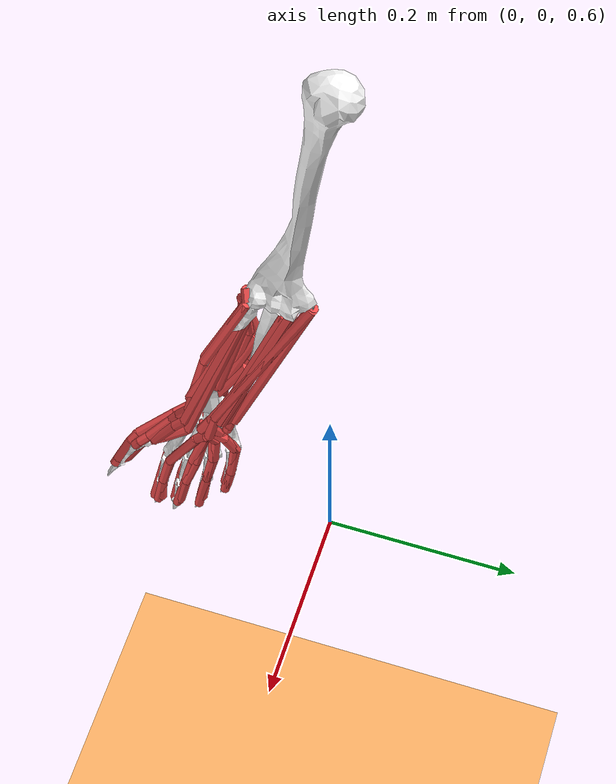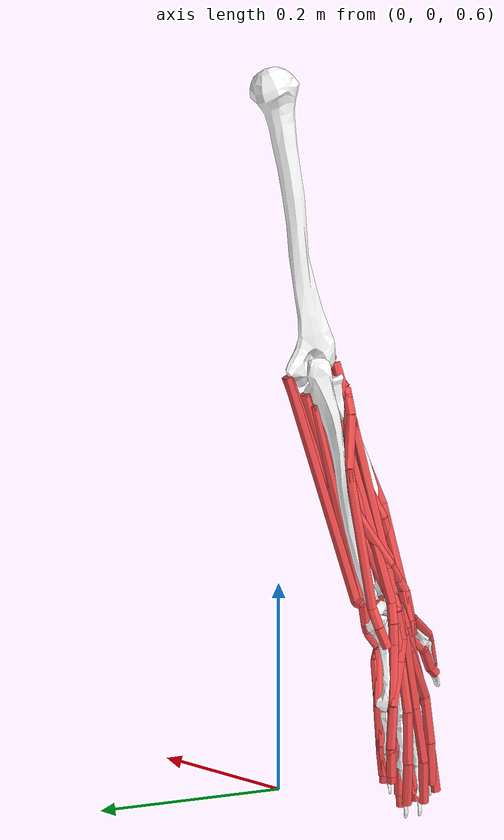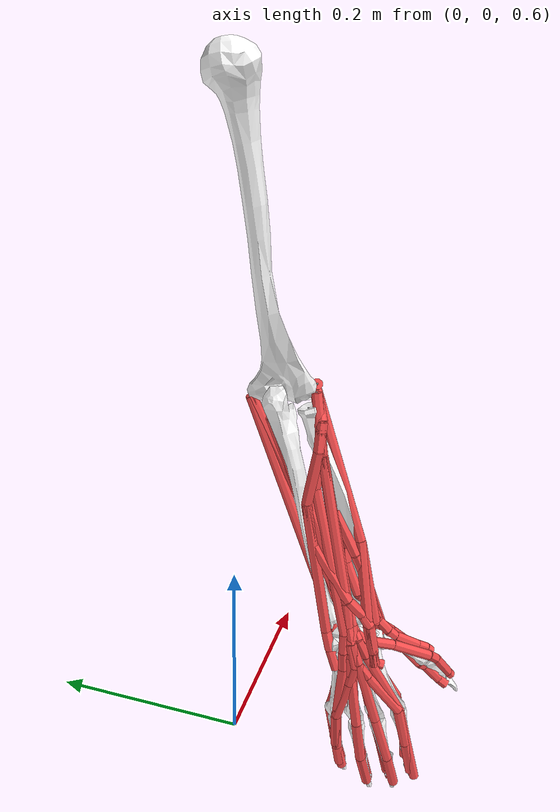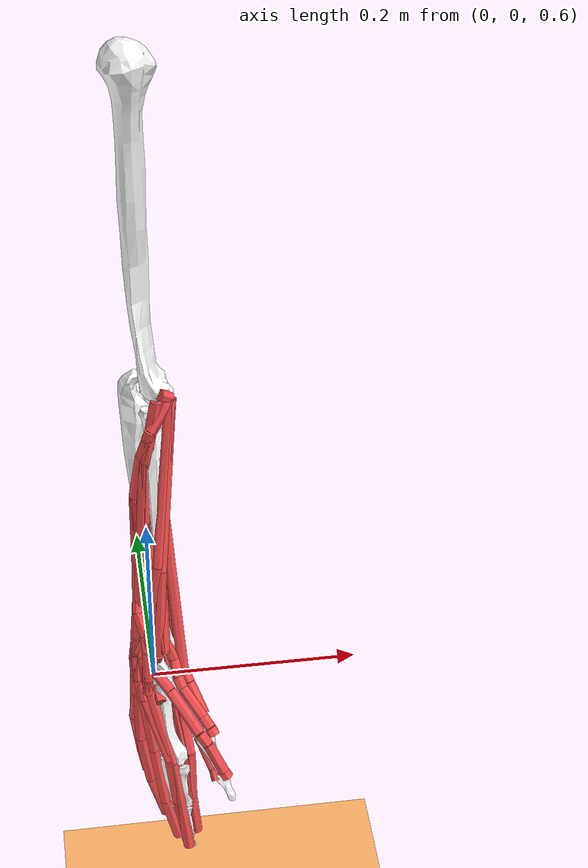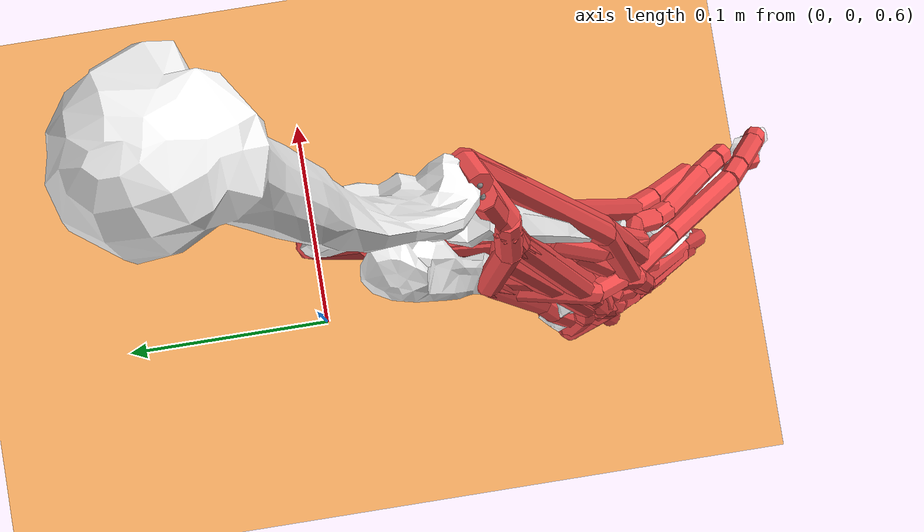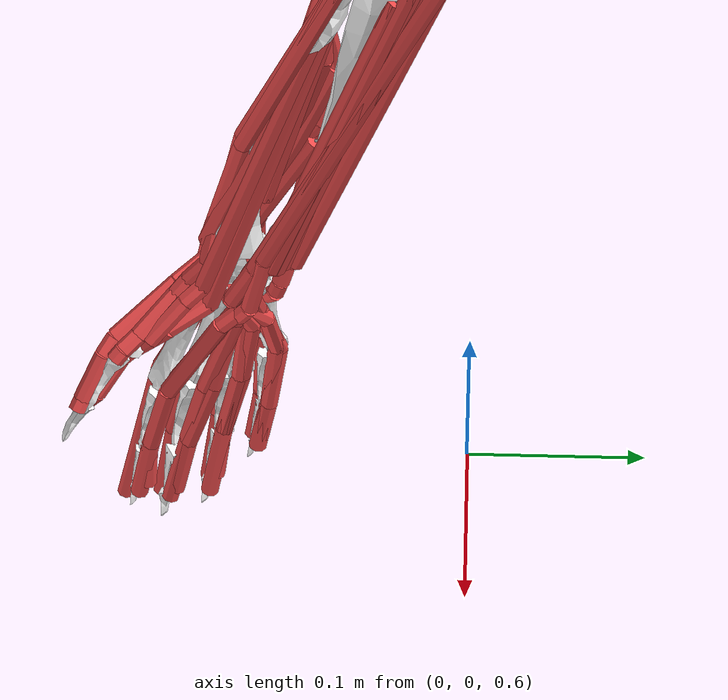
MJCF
<mujoco model="template">
  <!-- This model has been converted from an OpenSim model. Model conversion by MyoConverter https://github.com/MyoHub/myoconverter. This model is licensed under Apache 2.0. -->
  <compiler angle="radian" autolimits="true"/>
  <option timestep="0.005"/>
  <size njmax="1000" nconmax="400" nkey="1" nuser_jnt="1"/>
  <visual>
    <scale framelength="0.5" framewidth="0.01"/>
  </visual>
  <statistic meansize="0.0480678" extent="2.30764" center="0 0 0.153819"/>
  <default class="main">
    <joint limited="true" armature="1e-05" damping="0.05"/>
    <geom margin="0.001" rgba="0.8 0.6 0.4 1"/>
    <site size="0.001 0.005 0.005"/>
    <tendon limited="false" width="0.005" rgba="0.95 0.3 0.3 1"/>
    <default class="muscle">
      <general ctrllimited="true" ctrlrange="0 1" dyntype="muscle" gaintype="muscle" biastype="muscle" dynprm="0.01 0.04 0 0 0 0 0 0 0 0" gainprm="0.75 1.05 -1 200 0.5 1.6 1.5 1.3 1.2 0" biasprm="0.75 1.05 -1 200 0.5 1.6 1.5 1.3 1.2 0"/>
    </default>
    <default class="motor">
      <general gainprm="5 0 0 0 0 0 0 0 0 0"/>
    </default>
  </default>
  <asset>
    <texture type="skybox" builtin="gradient" rgb1="1 1 1" rgb2="0.6 0.8 1" width="256" height="1536"/>
    <mesh name="ground_geom_1_humerus" file="Geometry\humerus.stl"/>
    <mesh name="ulna_geom_1_ulna" file="Geometry\ulna.stl"/>
    <mesh name="radius_geom_1_radius" file="Geometry\radius.stl"/>
    <mesh name="trapezium_geom_1_r_trpzm" file="Geometry\r_trpzm.stl"/>
    <mesh name="trapezoid_geom_1_r_trpzd" file="Geometry\r_trpzd.stl"/>
    <mesh name="capitate_geom_1_r_cap" file="Geometry\r_cap.stl"/>
    <mesh name="hamate_geom_1_r_ham" file="Geometry\r_ham.stl"/>
    <mesh name="metacarpal2_geom_1_fingers1" file="Geometry\fingers1.stl"/>
    <mesh name="Iphalanx1_geom_1_fingers2" file="Geometry\fingers2.stl"/>
    <mesh name="Iphalanx2_geom_1_fingers3" file="Geometry\fingers3.stl"/>
    <mesh name="Iphalanx3_geom_1_fingers4" file="Geometry\fingers4.stl"/>
    <mesh name="metacarpal3_geom_1_fingers8" file="Geometry\fingers8.stl"/>
    <mesh name="midfinger_geom_1_fingers6" file="Geometry\fingers6.stl"/>
    <mesh name="midfinger_geom_2_fingers7" file="Geometry\fingers7.stl"/>
    <mesh name="midfinger_geom_3_fingers5" file="Geometry\fingers5.stl"/>
    <mesh name="metacarpal4_geom_1_fingers12" file="Geometry\fingers12.stl"/>
    <mesh name="ringfinger_geom_1_fingers10" file="Geometry\fingers10.stl"/>
    <mesh name="ringfinger_geom_2_fingers11" file="Geometry\fingers11.stl"/>
    <mesh name="ringfinger_geom_3_fingers9" file="Geometry\fingers9.stl"/>
    <mesh name="metacarpal5_geom_1_fingers16" file="Geometry\fingers16.stl"/>
    <mesh name="littlefinger_geom_1_fingers14" file="Geometry\fingers14.stl"/>
    <mesh name="littlefinger_geom_2_fingers15" file="Geometry\fingers15.stl"/>
    <mesh name="littlefinger_geom_3_fingers13" file="Geometry\fingers13.stl"/>
    <mesh name="thumb_geom_1_fingers17" file="Geometry\fingers17.stl"/>
    <mesh name="thumb_geom_2_fingers18" file="Geometry\fingers18.stl"/>
    <mesh name="thumb_geom_3_fingers19" file="Geometry\fingers19.stl"/>
    <mesh name="scaphoid_geom_1_r_scaph" file="Geometry\r_scaph.stl"/>
    <mesh name="lunate_geom_1_r_lun" file="Geometry\r_lun.stl"/>
    <mesh name="pisiform_geom_1_r_pis" file="Geometry\r_pis.stl"/>
    <mesh name="triquetrum_geom_1_r_triq" file="Geometry\r_triq.stl"/>
  </asset>
  <worldbody>
    <light pos="0 0 0" dir="0 0 -1" directional="true"/>
    <body name="ground" quat="0.707035 0.707179 0 0">
      <geom name="ground-plane" size="10 10 0.125" quat="0.707035 -0.707179 0 0" type="plane" rgba="1 0.7 0.4 1"/>
      <geom name="ground_geom_1" pos="0 1.274 0" type="mesh" rgba="1 1 1 1" mesh="ground_geom_1_humerus"/>
      <site name="FCR_FCR-P1" pos="0.00639 0.99639 0.01313"/>
      <site name="FCU_FCU-P1" pos="0.00463 0.99632 0.01318"/>
      <site name="ECU_pre-surgery_ECU_pre-surgery-P1" pos="0.02268 1.00596 0.06679"/>
      <site name="ECU_post-surgery_ECU_post-surgery-P1" pos="0.02268 1.00596 0.06679"/>
      <site name="EDM_EDM-P1" pos="0.02257 1.00608 0.06683"/>
      <site name="ECRB_ECRB-P1" pos="0.02254 1.00587 0.06679"/>
      <site name="ECRL_ECRL-P1" pos="0.01337 1.01289 0.07069"/>
      <site name="ECRL_ECRL-P2" pos="0.02239 1.00566 0.06679"/>
      <site name="FDSI_FDSI-P1" pos="0.0035 0.97945 0.03226"/>
      <site name="FDSM_FDSM-P1" pos="0.0035 0.97945 0.03226"/>
      <site name="FDSR_FDSR-P1" pos="0.0035 0.97945 0.03226"/>
      <site name="FDSL_FDSL-P1" pos="0.0035 0.97945 0.03226"/>
      <site name="EDCL_EDCL-P1" pos="0.01056 1.00611 0.07127"/>
      <site name="EDCR_EDCR-P1" pos="0.01011 1.00611 0.07127"/>
      <site name="EDCM_EDCM-P1" pos="0.01011 1.00611 0.07127"/>
      <site name="EDCI_EDCI-P1" pos="0.01011 1.00611 0.07127"/>
      <site name="PL_PL-P1" pos="0.00468 0.99702 0.01316"/>
    </body>
    <body name="ulna" pos="0.0127 -0.0389 1" quat="0.707035 0.707179 0 0">
      <inertial pos="0 0 0" mass="0.001" diaginertia="0.001 0.001 0.001"/>
      <joint name="elbow_flexion" pos="0 0 0" axis="0.226004 0.191003 0.955217" limited="false" range="0 2.269" damping="0"/>
      <geom name="ulna_geom_1" type="mesh" rgba="1 1 1 1" mesh="ulna_geom_1_ulna"/>
      <site name="FCU_FCU-P2" pos="-0.00465 -0.22771 0.05589"/>
      <site name="FCU_FCU-P3" pos="-0.01368 -0.22899 0.05805"/>
      <site name="ECU_pre-surgery_ECU_pre-surgery-P4" pos="-0.02457 -0.09422 0.03348"/>
      <site name="ECU_pre-surgery_ECU_pre-surgery-P5" pos="-0.02793 -0.23106 0.05873"/>
      <site name="ECU_post-surgery_ECU_post-surgery-P4" pos="-0.02457 -0.09422 0.03348"/>
      <site name="ECU_post-surgery_ECU_post-surgery-P5" pos="-0.02463 -0.1364 0.04159"/>
      <site name="ECU_post-surgery_ECU_post-surgery-P6" pos="-0.02953 -0.18933 0.07846"/>
      <site name="EDM_EDM-P4" pos="-0.03277 -0.22628 0.07769"/>
      <site name="FDPI_FDPI-P1" pos="-0.0113 -0.03157 0.00208"/>
      <site name="FDPM_FDPM-P1" pos="-0.0113 -0.03157 0.00208"/>
      <site name="FDPR_FDPR-P1" pos="-0.0113 -0.03157 0.00208"/>
      <site name="FDPL_FDPL-P1" pos="-0.0113 -0.03157 0.00208"/>
      <site name="EPL_EPL-P1" pos="-0.02127 -0.0916 0.03268"/>
      <site name="EIP_EIP-P1" pos="-0.01974 -0.14668 0.04449"/>
      <body name="radius" pos="-0.0065 -0.008 0.027">
        <inertial pos="0 0 0" mass="0.001" diaginertia="0.001 0.001 0.001"/>
        <joint name="pro_sup" pos="0 0 0" axis="0.0563992 0.983586 -0.171398" limited="false" range="-1.571 1.571"/>
        <geom name="radius_geom_1" type="mesh" rgba="1 1 1 1" mesh="radius_geom_1_radius"/>
        <site name="FCR_FCR-P2" pos="0.00953 -0.21667 0.05024"/>
        <site name="ECU_pre-surgery_ECU_pre-surgery-P2" pos="-0.00239 -0.01019 0.01329"/>
        <site name="ECU_pre-surgery_ECU_pre-surgery-P3" pos="-0.01094 -0.03546 0.01362"/>
        <site name="ECU_post-surgery_ECU_post-surgery-P2" pos="-0.00239 -0.01019 0.01329"/>
        <site name="ECU_post-surgery_ECU_post-surgery-P3" pos="-0.01094 -0.03546 0.01362"/>
        <site name="ECU_post-surgery_ECU_post-surgery-P7" pos="-0.01789 -0.19788 0.06459"/>
        <site name="ECU_post-surgery_ECU_post-surgery-P8" pos="-0.01779 -0.20954 0.07234"/>
        <site name="EDM_EDM-P2" pos="-0.00523 -0.01802 0.01357"/>
        <site name="EDM_EDM-P3" pos="-0.01075 -0.07282 0.01237"/>
        <site name="ECRB_ECRB-P2" pos="-0.00384 -0.1248 0.05482"/>
        <site name="ECRB_ECRB-P3" pos="-0.01733 -0.20892 0.0704"/>
        <site name="ECRL_ECRL-P3" pos="-0.00136 -0.12953 0.05532"/>
        <site name="ECRL_ECRL-P4" pos="-0.0083 -0.21052 0.0752"/>
        <site name="FDSI_FDSI-P2" pos="0.01091 -0.21436 0.04048"/>
        <site name="FDSI_FDSI-P3" pos="0.00183 -0.21671 0.04253"/>
        <site name="FDSM_FDSM-P2" pos="0.01048 -0.21423 0.03978"/>
        <site name="FDSM_FDSM-P3" pos="0.0019 -0.2167 0.0438"/>
        <site name="FDSR_FDSR-P2" pos="0.01037 -0.21504 0.03862"/>
        <site name="FDSR_FDSR-P3" pos="-0.00037 -0.21764 0.0409"/>
        <site name="FDSL_FDSL-P2" pos="0.01048 -0.21423 0.03978"/>
        <site name="FDSL_FDSL-P3" pos="0.001 -0.2177 0.0418"/>
        <site name="FDPI_FDPI-P2" pos="0.00797 -0.21647 0.04395"/>
        <site name="FDPI_FDPI-P3" pos="0.0013 -0.21659 0.04619"/>
        <site name="FDPM_FDPM-P2" pos="0.00433 -0.21689 0.0427"/>
        <site name="FDPM_FDPM-P3" pos="-0.00152 -0.21639 0.04445"/>
        <site name="FDPR_FDPR-P2" pos="0.00438 -0.21834 0.03741"/>
        <site name="FDPR_FDPR-P3" pos="-0.00261 -0.217 0.04286"/>
        <site name="FDPL_FDPL-P2" pos="0.00377 -0.21886 0.03584"/>
        <site name="FDPL_FDPL-P3" pos="-0.0015 -0.217 0.0433"/>
        <site name="EDCL_EDCL-P2" pos="-0.0082 -0.04004 0.01668"/>
        <site name="EDCL_EDCL-P3" pos="-0.01974 -0.18469 0.04807"/>
        <site name="EDCL_EDCL-P4" pos="-0.02211 -0.21097 0.05287"/>
        <site name="EDCR_EDCR-P2" pos="-0.0082 -0.04004 0.01668"/>
        <site name="EDCR_EDCR-P3" pos="-0.01766 -0.18446 0.04898"/>
        <site name="EDCR_EDCR-P4" pos="-0.02021 -0.21054 0.05596"/>
        <site name="EDCM_EDCM-P2" pos="-0.0082 -0.04004 0.01668"/>
        <site name="EDCM_EDCM-P3" pos="-0.01675 -0.18466 0.04682"/>
        <site name="EDCM_EDCM-P4" pos="-0.01933 -0.21054 0.05152"/>
        <site name="EDCI_EDCI-P2" pos="-0.0082 -0.04004 0.01668"/>
        <site name="EDCI_EDCI-P3" pos="-0.02209 -0.18446 0.04898"/>
        <site name="EDCI_EDCI-P4" pos="-0.02376 -0.21054 0.0533"/>
        <site name="FPL_FPL-P1" pos="-0.00284 -0.09605 0.02992"/>
        <site name="FPL_FPL-P2" pos="-0.00166 -0.13532 0.04257"/>
        <site name="FPL_FPL-P3" pos="-0.00037 -0.16882 0.04439"/>
        <site name="APL_APL-P1" pos="-0.00494 -0.09677 0.03004"/>
        <site name="APL_APL-P2" pos="-0.00892 -0.13772 0.05255"/>
        <site name="APL_APL-P3" pos="-0.0066 -0.15947 0.06132"/>
        <site name="APL_APL-P4" pos="-0.00682 -0.17731 0.06462"/>
        <site name="APL_APL-P5" pos="-0.00282 -0.20831 0.07607"/>
        <site name="EPB_EPB-P1" pos="-0.00294 -0.13573 0.04196"/>
        <site name="EPB_EPB-P2" pos="-0.00701 -0.14896 0.04387"/>
        <site name="EPB_EPB-P3" pos="-0.01283 -0.17881 0.05817"/>
        <site name="EPB_EPB-P4" pos="-0.00547 -0.19041 0.06961"/>
        <site name="EPB_EPB-P5" pos="0.00469 -0.21769 0.0756"/>
        <site name="EPL_EPL-P2" pos="-0.01652 -0.16952 0.03814"/>
        <site name="EPL_EPL-P3" pos="-0.01762 -0.20537 0.0523"/>
        <site name="EIP_EIP-P2" pos="-0.01612 -0.20811 0.05228"/>
        <site name="PL_PL-P2" pos="0.01122 -0.20758 0.04487"/>
        <body name="rotaxis" pos="-0.0085 -0.2313 0.0561" quat="0.972394 -0.128018 0.193422 -0.0254645">
          <inertial pos="0 0 0" mass="0.001" diaginertia="0.001 0.001 0.001"/>
          <body name="auxprfem" pos="-0.001 0.009 0">
            <inertial pos="0 0 0" mass="0.001" diaginertia="0.001 0.001 0.001"/>
            <joint name="rotaxis_auxprfem_r3" pos="0 0 0" axis="0 0 1" limited="false" range="-100000 100000"/>
            <body name="auxprrud">
              <inertial pos="0 0 0" mass="0.001" diaginertia="0.001 0.001 0.001"/>
              <joint name="auxprfem-auxprrud_coord" pos="0 0 0" axis="1 0 0" limited="false" range="-0.4363 0.6109"/>
              <body name="auxdrfem" pos="0.001 -0.02 0">
                <inertial pos="0 0 0" mass="0.001" diaginertia="0.001 0.001 0.001"/>
                <joint name="auxprrud_auxdrfem_r3" pos="0 0 0" axis="0 0 1" limited="false" range="-100000 100000"/>
                <body name="auxdrrud">
                  <inertial pos="0 0 0" mass="0.001" diaginertia="0.001 0.001 0.001"/>
                  <joint name="auxdrfem_auxdrrud_r1" pos="0 0 0" axis="1 0 0" limited="false" range="-100000 100000"/>
                  <body name="trapezium" pos="0.0035 -0.0035 0.02" quat="0.991445 -0.130526 0 0">
                    <inertial pos="0 0 0" mass="0.001" diaginertia="0.001 0.001 0.001"/>
                    <geom name="trapezium_geom_1" type="mesh" rgba="1 1 1 1" mesh="trapezium_geom_1_r_trpzm"/>
                    <site name="APL_APL-P7" pos="0.00722 0.00906 0.01082"/>
                    <site name="EPB_EPB-P6" pos="-0.00078 0.00458 0.01475"/>
                  </body>
                  <body name="trapezoid" pos="-0.0015 -0.0044 0.0134" quat="0.981059 0.173004 -0.0858152 -0.0151331">
                    <inertial pos="0 0 0" mass="0.001" diaginertia="0.001 0.001 0.001"/>
                    <geom name="trapezoid_geom_1" type="mesh" rgba="1 1 1 1" mesh="trapezoid_geom_1_r_trpzd"/>
                    <site name="FCR_FCR-P3" pos="0.01395 -0.0012 -0.0067"/>
                    <site name="ECU_post-surgery_ECU_post-surgery-P9" pos="-0.01575 0.00302 0.00216"/>
                    <site name="ECRB_ECRB-P4" pos="-0.01598 0.00257 0.00197"/>
                  </body>
                  <body name="capitate" pos="-0.0155 -0.0018 -0.0055" quat="0.996196 0.0871393 0 0">
                    <inertial pos="0 0 0" mass="0.001" diaginertia="0.001 0.001 0.001"/>
                    <geom name="capitate_geom_1" type="mesh" rgba="1 1 1 1" mesh="capitate_geom_1_r_cap"/>
                    <site name="FDSI_FDSI-P6" pos="0.02944 -0.01143 0.00869"/>
                    <site name="FDSM_FDSM-P6" pos="0.03 -0.0118 0.0084"/>
                    <site name="FDSR_FDSR-P6" pos="0.0289 -0.0155 0.0073"/>
                    <site name="FDSL_FDSL-P6" pos="0.0268 -0.0129 0.0061"/>
                    <site name="FDPI_FDPI-P4" pos="0.02269 0.01117 0.00347"/>
                    <site name="FDPI_FDPI-P5" pos="0.02499 0.00065 0.00589"/>
                    <site name="FDPM_FDPM-P4" pos="0.02125 0.01055 0.00154"/>
                    <site name="FDPM_FDPM-P5" pos="0.02346 0.00125 0.00384"/>
                    <site name="FDPR_FDPR-P4" pos="0.0238 0.01117 -0.00097"/>
                    <site name="FDPR_FDPR-P5" pos="0.02829 0.00175 0.00473"/>
                    <site name="FDPL_FDPL-P4" pos="0.02424 0.01233 0.0008"/>
                    <site name="FDPL_FDPL-P5" pos="0.02829 0.00175 0.00473"/>
                    <site name="EDCL_EDCL-P6" pos="-0.00192 -0.01151 0.00084"/>
                    <site name="EDCI_EDCI-P6" pos="-0.00196 -0.00655 0.00232"/>
                    <site name="PL_PL-P3" pos="0.03689 0.00135 0.00732"/>
                    <body name="FDSI_FDSI-P4">
                      <joint name="FDSI_FDSI-P4_x" pos="0 0 0" axis="1 0 0" type="slide" range="0.02244 0.02944"/>
                      <joint name="FDSI_FDSI-P4_y" pos="0 0 0" axis="0 1 0" type="slide" range="-0.01143 0.01397"/>
                      <joint name="FDSI_FDSI-P4_z" pos="0 0 0" axis="0 0 1" type="slide" range="0.00139 0.00869"/>
                      <geom size="0.0005" contype="2" conaffinity="2" rgba="0 0 1 0"/>
                      <site name="FDSI_FDSI-P4" pos="0 0 0"/>
                    </body>
                    <body name="FDSI_FDSI-P5">
                      <joint name="FDSI_FDSI-P5_x" pos="0 0 0" axis="1 0 0" type="slide" range="0.02703 0.02944"/>
                      <joint name="FDSI_FDSI-P5_y" pos="0 0 0" axis="0 1 0" type="slide" range="-0.01143 0.00411"/>
                      <joint name="FDSI_FDSI-P5_z" pos="0 0 0" axis="0 0 1" type="slide" range="0.00444 0.00869"/>
                      <geom size="0.0005" contype="2" conaffinity="2" rgba="0 0 1 0"/>
                      <site name="FDSI_FDSI-P5" pos="0 0 0"/>
                    </body>
                    <body name="FDSM_FDSM-P4">
                      <joint name="FDSM_FDSM-P4_x" pos="0 0 0" axis="1 0 0" type="slide" range="0.02277 0.03"/>
                      <joint name="FDSM_FDSM-P4_y" pos="0 0 0" axis="0 1 0" type="slide" range="-0.0118 0.01364"/>
                      <joint name="FDSM_FDSM-P4_z" pos="0 0 0" axis="0 0 1" type="slide" range="0.00172 0.0084"/>
                      <geom size="0.0005" contype="2" conaffinity="2" rgba="0 0 1 0"/>
                      <site name="FDSM_FDSM-P4" pos="0 0 0"/>
                    </body>
                    <body name="FDSM_FDSM-P5">
                      <joint name="FDSM_FDSM-P5_x" pos="0 0 0" axis="1 0 0" type="slide" range="0.0269 0.03"/>
                      <joint name="FDSM_FDSM-P5_y" pos="0 0 0" axis="0 1 0" type="slide" range="-0.0118 0.0054"/>
                      <joint name="FDSM_FDSM-P5_z" pos="0 0 0" axis="0 0 1" type="slide" range="0.0037 0.0084"/>
                      <geom size="0.0005" contype="2" conaffinity="2" rgba="0 0 1 0"/>
                      <site name="FDSM_FDSM-P5" pos="0 0 0"/>
                    </body>
                    <body name="FDSR_FDSR-P4">
                      <joint name="FDSR_FDSR-P4_x" pos="0 0 0" axis="1 0 0" type="slide" range="0.02189 0.0289"/>
                      <joint name="FDSR_FDSR-P4_y" pos="0 0 0" axis="0 1 0" type="slide" range="-0.0155 0.01306"/>
                      <joint name="FDSR_FDSR-P4_z" pos="0 0 0" axis="0 0 1" type="slide" range="0.00048 0.0073"/>
                      <geom size="0.0005" contype="2" conaffinity="2" rgba="0 0 1 0"/>
                      <site name="FDSR_FDSR-P4" pos="0 0 0"/>
                    </body>
                    <body name="FDSR_FDSR-P5">
                      <joint name="FDSR_FDSR-P5_x" pos="0 0 0" axis="1 0 0" type="slide" range="0.02545 0.0289"/>
                      <joint name="FDSR_FDSR-P5_y" pos="0 0 0" axis="0 1 0" type="slide" range="-0.0155 0.00479"/>
                      <joint name="FDSR_FDSR-P5_z" pos="0 0 0" axis="0 0 1" type="slide" range="0.0023 0.0073"/>
                      <geom size="0.0005" contype="2" conaffinity="2" rgba="0 0 1 0"/>
                      <site name="FDSR_FDSR-P5" pos="0 0 0"/>
                    </body>
                    <body name="FDSL_FDSL-P4">
                      <joint name="FDSL_FDSL-P4_x" pos="0 0 0" axis="1 0 0" type="slide" range="0.02201 0.0268"/>
                      <joint name="FDSL_FDSL-P4_y" pos="0 0 0" axis="0 1 0" type="slide" range="-0.0129 0.01258"/>
                      <joint name="FDSL_FDSL-P4_z" pos="0 0 0" axis="0 0 1" type="slide" range="-0.00027 0.0061"/>
                      <geom size="0.0005" contype="2" conaffinity="2" rgba="0 0 1 0"/>
                      <site name="FDSL_FDSL-P4" pos="0 0 0"/>
                    </body>
                    <body name="FDSL_FDSL-P5">
                      <joint name="FDSL_FDSL-P5_x" pos="0 0 0" axis="1 0 0" type="slide" range="0.0255 0.0268"/>
                      <joint name="FDSL_FDSL-P5_y" pos="0 0 0" axis="0 1 0" type="slide" range="-0.0129 0.0021"/>
                      <joint name="FDSL_FDSL-P5_z" pos="0 0 0" axis="0 0 1" type="slide" range="0.0025 0.0061"/>
                      <geom size="0.0005" contype="2" conaffinity="2" rgba="0 0 1 0"/>
                      <site name="FDSL_FDSL-P5" pos="0 0 0"/>
                    </body>
                  </body>
                  <body name="hamate" pos="-0.006 -0.005 -0.0175" quat="0.994524 -0.104509 0 0">
                    <inertial pos="0 0 0" mass="0.001" diaginertia="0.001 0.001 0.001"/>
                    <geom name="hamate_geom_1" type="mesh" rgba="1 1 1 1" mesh="hamate_geom_1_r_ham"/>
                    <site name="FCU_FCU-P4" pos="0.01901 0.0109 0.00261"/>
                    <site name="FCU_FCU-P5" pos="0.01899 0.0024 0.0012"/>
                  </body>
                  <body name="carp_metacarp">
                    <inertial pos="0 0 0" mass="0.001" diaginertia="0.001 0.001 0.001"/>
                    <body name="metacarpal2" pos="-0.0047 -0.0095 -0.005" quat="0.987673 0.0863939 0.13003 0.011374">
                      <inertial pos="0 0 0" mass="0.001" diaginertia="0.001 0.001 0.001"/>
                      <geom name="metacarpal2_geom_1" type="mesh" rgba="1 1 1 1" mesh="metacarpal2_geom_1_fingers1"/>
                      <site name="FCR_FCR-P4" pos="0.00592 0.00269 0.01328"/>
                      <site name="ECRL_ECRL-P6" pos="-0.01108 -0.01106 0.02568"/>
                      <site name="FDSI_FDSI-P7" pos="0.01297 -0.01437 0.02183"/>
                      <site name="FDSI_FDSI-P8" pos="0.00543 -0.06688 0.04728"/>
                      <site name="FDPI_FDPI-P6" pos="0.013 -0.0048 0.01072"/>
                      <site name="FDPI_FDPI-P7" pos="0.00363 -0.06662 0.0449"/>
                      <site name="EDCI_EDCI-P8" pos="-0.01225 -0.06926 0.04042"/>
                      <site name="EIP_EIP-P4" pos="-0.01312 0.00595 0.0075"/>
                      <site name="EIP_EIP-P5" pos="-0.01022 -0.07179 0.04293"/>
                      <body name="Iphalanx1" pos="-0.002402 -0.0685 0.045">
                        <inertial pos="0 0 0" mass="0.001" diaginertia="0.001 0.001 0.001"/>
                        <joint name="MCP2_lateral" pos="0 0 0" axis="1 0 0" limited="false" range="-0.3491 0.3491"/>
                        <joint name="MCP2_flex" pos="0 0 0" axis="0 0 1" limited="false" range="-0.1745 1.571"/>
                        <geom name="Iphalanx1_geom_1" type="mesh" rgba="1 1 1 1" mesh="Iphalanx1_geom_1_fingers2"/>
                        <site name="FDSI_FDSI-P9" pos="0.00596 -0.04624 0.00883"/>
                        <site name="FDPI_FDPI-P8" pos="0.00494 -0.0506 0.00914"/>
                        <site name="EDCI_EDCI-P9" pos="-0.00658 -0.04852 0.0044"/>
                        <body name="Iphalanx2" pos="0.0005 -0.04826 0.00799">
                          <inertial pos="0 0 0" mass="0.001" diaginertia="0.001 0.001 0.001"/>
                          <joint name="PIP_flex" pos="0 0 0" axis="0 0 1" limited="false" range="-0.08727 1.571"/>
                          <geom name="Iphalanx2_geom_1" type="mesh" rgba="1 1 1 1" mesh="Iphalanx2_geom_1_fingers3"/>
                          <site name="FDPI_FDPI-P9" pos="0.0095 -0.03028 0.00343"/>
                          <body name="Iphalanx3" pos="0.00193 -0.03277 0.00472">
                            <inertial pos="0 0 0" mass="0.001" diaginertia="0.001 0.001 0.001"/>
                            <joint name="DIP_flex" pos="0 0 0" axis="0 0 1" limited="false" range="-0.08727 1.571"/>
                            <geom name="Iphalanx3_geom_1" type="mesh" rgba="1 1 1 1" mesh="Iphalanx3_geom_1_fingers4"/>
                            <site name="FDSI_FDSI-P10" pos="0.00581 -0.0059 0.00263"/>
                            <site name="EDCI_EDCI-P10" pos="-0.00291 -0.01043 7e-05"/>
                            <site name="EIP_EIP-P6" pos="-0.00452 -0.0182 0.00396"/>
                          </body>
                        </body>
                      </body>
                      <body name="ECRL_ECRL-P5">
                        <joint name="ECRL_ECRL-P5_x" pos="0 0 0" axis="1 0 0" type="slide" range="-0.01349 -0.01108"/>
                        <joint name="ECRL_ECRL-P5_y" pos="0 0 0" axis="0 1 0" type="slide" range="-0.01106 0.01118"/>
                        <joint name="ECRL_ECRL-P5_z" pos="0 0 0" axis="0 0 1" type="slide" range="0.02204 0.02568"/>
                        <geom size="0.0005" contype="2" conaffinity="2" rgba="0 0 1 0"/>
                        <site name="ECRL_ECRL-P5" pos="0 0 0"/>
                      </body>
                    </body>
                    <body name="metacarpal3" pos="-0.0047 -0.0085 -0.005" quat="0.994135 0.0472114 0.085078 0.0472114">
                      <inertial pos="0 0 0" mass="0.001" diaginertia="0.001 0.001 0.001"/>
                      <geom name="metacarpal3_geom_1" type="mesh" rgba="1 1 1 1" mesh="metacarpal3_geom_1_fingers8"/>
                      <site name="ECU_post-surgery_ECU_post-surgery-P10" pos="-0.01502 -0.00464 0.01507"/>
                      <site name="ECRB_ECRB-P5" pos="-0.01528 -0.00506 0.01554"/>
                      <site name="FDSM_FDSM-P7" pos="0.0144 -0.01632 0.01008"/>
                      <site name="FDSM_FDSM-P8" pos="0.00429 -0.08012 0.01596"/>
                      <site name="FDSR_FDSR-P7" pos="0.0144 -0.0252 -0.00101"/>
                      <site name="FDPM_FDPM-P6" pos="0.01168 -0.00745 0.00755"/>
                      <site name="FDPM_FDPM-P7" pos="0.00765 -0.07598 0.01288"/>
                      <site name="FDPR_FDPR-P6" pos="0.01263 -0.0153 0.00166"/>
                      <site name="EDCL_EDCL-P7" pos="-0.01096 -0.02472 -0.01035"/>
                      <site name="EDCR_EDCR-P6" pos="-0.00903 0.00837 -0.00741"/>
                      <site name="EDCM_EDCM-P7" pos="-0.01348 -0.07696 0.01108"/>
                      <site name="EDCI_EDCI-P7" pos="-0.01421 -0.01886 0.0078"/>
                      <site name="PL_PL-P4" pos="0.00932 -0.02377 0.00981"/>
                      <body name="midfinger" pos="0 -0.003 0">
                        <inertial pos="0 0 0" mass="0.001" diaginertia="0.001 0.001 0.001"/>
                        <geom name="midfinger_geom_1" type="mesh" rgba="1 1 1 1" mesh="midfinger_geom_1_fingers6"/>
                        <geom name="midfinger_geom_2" type="mesh" rgba="1 1 1 1" mesh="midfinger_geom_2_fingers7"/>
                        <geom name="midfinger_geom_3" type="mesh" rgba="1 1 1 1" mesh="midfinger_geom_3_fingers5"/>
                        <site name="FDSM_FDSM-P9" pos="-0.00048 -0.12516 0.01851"/>
                        <site name="FDSM_FDSM-P10" pos="0.00028 -0.17254 0.02483"/>
                        <site name="FDPM_FDPM-P8" pos="0.00087 -0.1259 0.01853"/>
                        <site name="FDPM_FDPM-P9" pos="0.00142 -0.16485 0.0224"/>
                        <site name="EDCM_EDCM-P8" pos="-0.01347 -0.13109 0.01966"/>
                        <site name="EDCM_EDCM-P9" pos="-0.00737 -0.17492 0.02576"/>
                      </body>
                      <body name="EDCM_EDCM-P6" pos="-0.01348 0 0">
                        <joint name="EDCM_EDCM-P6_y" pos="0 0 0" axis="0 1 0" type="slide" range="-0.07696 0.00659"/>
                        <joint name="EDCM_EDCM-P6_z" pos="0 0 0" axis="0 0 1" type="slide" range="-0.00208 0.01108"/>
                        <geom size="0.0005" contype="2" conaffinity="2" rgba="0 0 1 0"/>
                        <site name="EDCM_EDCM-P6" pos="0 0 0"/>
                      </body>
                    </body>
                    <body name="metacarpal4" pos="-0.0047 -0.008 -0.0033" quat="0.994135 0.0472114 0.085078 0.0472114">
                      <inertial pos="0 0 0" mass="0.001" diaginertia="0.001 0.001 0.001"/>
                      <geom name="metacarpal4_geom_1" type="mesh" rgba="1 1 1 1" mesh="metacarpal4_geom_1_fingers12"/>
                      <site name="FDSR_FDSR-P8" pos="0.00807 -0.07635 -0.00696"/>
                      <site name="FDSL_FDSL-P7" pos="0.01463 -0.02498 -0.01151"/>
                      <site name="FDPR_FDPR-P7" pos="0.00788 -0.07665 -0.0056"/>
                      <site name="FDPL_FDPL-P6" pos="0.01286 -0.01597 -0.00617"/>
                      <site name="EDCR_EDCR-P7" pos="-0.01378 -0.07606 -0.01001"/>
                      <body name="ringfinger" pos="0 -0.0025 0">
                        <inertial pos="0 0 0" mass="0.001" diaginertia="0.001 0.001 0.001"/>
                        <geom name="ringfinger_geom_1" type="mesh" rgba="1 1 1 1" mesh="ringfinger_geom_1_fingers10"/>
                        <geom name="ringfinger_geom_2" type="mesh" rgba="1 1 1 1" mesh="ringfinger_geom_2_fingers11"/>
                        <geom name="ringfinger_geom_3" type="mesh" rgba="1 1 1 1" mesh="ringfinger_geom_3_fingers9"/>
                        <site name="FDSR_FDSR-P9" pos="0.0033 -0.12455 -0.00441"/>
                        <site name="FDSR_FDSR-P10" pos="0.00672 -0.17283 0.00102"/>
                        <site name="FDPR_FDPR-P8" pos="0.00288 -0.12885 -0.0044"/>
                        <site name="FDPR_FDPR-P9" pos="0.00609 -0.15981 -0.0023"/>
                        <site name="EDCR_EDCR-P8" pos="-0.0088 -0.12604 -0.00859"/>
                        <site name="EDCR_EDCR-P9" pos="-0.00093 -0.16987 -0.00249"/>
                      </body>
                    </body>
                    <body name="metacarpal5" pos="-0.002 -0.01 0.0035" quat="0.994135 0.0472114 0.085078 0.0472114">
                      <inertial pos="0 0 0" mass="0.001" diaginertia="0.001 0.001 0.001"/>
                      <geom name="metacarpal5_geom_1" type="mesh" rgba="1 1 1 1" mesh="metacarpal5_geom_1_fingers16"/>
                      <site name="FCU_FCU-P6" pos="0.00845 -0.0091 -0.01963"/>
                      <site name="ECU_pre-surgery_ECU_pre-surgery-P7" pos="-0.00458 -0.00734 -0.02848"/>
                      <site name="EDM_EDM-P6" pos="-0.00895 -0.00546 -0.02267"/>
                      <site name="EDM_EDM-P7" pos="-0.00709 -0.06329 -0.03424"/>
                      <site name="FDSL_FDSL-P8" pos="0.00674 -0.06152 -0.0347"/>
                      <site name="FDPL_FDPL-P7" pos="0.00655 -0.06359 -0.03689"/>
                      <site name="EDCL_EDCL-P8" pos="-0.00801 -0.06389 -0.03508"/>
                      <body name="littlefinger" pos="0 -0.002 0">
                        <inertial pos="0 0 0" mass="0.001" diaginertia="0.001 0.001 0.001"/>
                        <geom name="littlefinger_geom_1" type="mesh" rgba="1 1 1 1" mesh="littlefinger_geom_1_fingers14"/>
                        <geom name="littlefinger_geom_2" type="mesh" rgba="1 1 1 1" mesh="littlefinger_geom_2_fingers15"/>
                        <geom name="littlefinger_geom_3" type="mesh" rgba="1 1 1 1" mesh="littlefinger_geom_3_fingers13"/>
                        <site name="EDM_EDM-P8" pos="-0.00281 -0.10702 -0.03713"/>
                        <site name="EDM_EDM-P9" pos="-0.00027 -0.13243 -0.0357"/>
                        <site name="FDSL_FDSL-P9" pos="0.0073 -0.10135 -0.0357"/>
                        <site name="FDSL_FDSL-P10" pos="0.00983 -0.13986 -0.03115"/>
                        <site name="FDPL_FDPL-P8" pos="0.00865 -0.10564 -0.03479"/>
                        <site name="FDPL_FDPL-P9" pos="0.0092 -0.13216 -0.03269"/>
                        <site name="EDCL_EDCL-P9" pos="-0.00303 -0.10372 -0.03765"/>
                        <site name="EDCL_EDCL-P10" pos="0.00129 -0.13957 -0.03333"/>
                      </body>
                    </body>
                    <body name="thumb" pos="0.008 -0.0045 0.0219">
                      <inertial pos="0 0 0" mass="0.001" diaginertia="0.001 0.001 0.001"/>
                      <joint name="thumb_abd" pos="0 0 0" axis="1 0 0" limited="false" range="-0.7854 0.2618"/>
                      <joint name="thumb_flex" pos="0 0 0" axis="0.0563992 0.983586 -0.171398" limited="false" range="-0.7854 1.571"/>
                      <geom name="thumb_geom_1" type="mesh" rgba="1 1 1 1" mesh="thumb_geom_1_fingers17"/>
                      <geom name="thumb_geom_2" type="mesh" rgba="1 1 1 1" mesh="thumb_geom_2_fingers18"/>
                      <geom name="thumb_geom_3" type="mesh" rgba="1 1 1 1" mesh="thumb_geom_3_fingers19"/>
                      <site name="FPL_FPL-P6" pos="0.0063 -0.0177 0.0199"/>
                      <site name="FPL_FPL-P7" pos="9e-05 -0.04175 0.03446"/>
                      <site name="FPL_FPL-P8" pos="0.00081 -0.04594 0.03877"/>
                      <site name="FPL_FPL-P9" pos="0.00577 -0.06923 0.04948"/>
                      <site name="FPL_FPL-P10" pos="0.00493 -0.07776 0.05542"/>
                      <site name="APL_APL-P8" pos="0.00384 0.00196 0.01452"/>
                      <site name="APL_APL-P9" pos="0.00816 -0.02324 0.03082"/>
                      <site name="EPB_EPB-P7" pos="-0.00387 0.00011 0.01647"/>
                      <site name="EPB_EPB-P8" pos="0.00452 -0.02214 0.03593"/>
                      <site name="EPB_EPB-P9" pos="0.0073 -0.03012 0.04408"/>
                      <site name="EPB_EPB-P10" pos="0.00871 -0.03603 0.048"/>
                      <site name="EPL_EPL-P6" pos="-0.0133 -0.00263 0.01214"/>
                      <site name="EPL_EPL-P7" pos="-0.00352 -0.03198 0.04462"/>
                      <site name="EPL_EPL-P8" pos="0.00081 -0.04107 0.05071"/>
                      <site name="EPL_EPL-P9" pos="0.00966 -0.06693 0.06022"/>
                      <site name="EPL_EPL-P10" pos="0.01228 -0.07282 0.06269"/>
                      <body name="FPL_FPL-P5" pos="0.00577 0 0">
                        <joint name="FPL_FPL-P5_y" pos="0 0 0" axis="0 1 0" type="slide" range="-0.0177 0.01018"/>
                        <joint name="FPL_FPL-P5_z" pos="0 0 0" axis="0 0 1" type="slide" range="-0.01528 0.0199"/>
                        <geom size="0.0005" contype="2" conaffinity="2" rgba="0 0 1 0"/>
                        <site name="FPL_FPL-P5" pos="0 0 0"/>
                      </body>
                    </body>
                  </body>
                </body>
              </body>
              <body name="scaphoid" pos="-0.0035 -0.0025 0.009" quat="0.979927 0.199355 0 0">
                <inertial pos="0 0 0" mass="0.001" diaginertia="0.001 0.001 0.001"/>
                <geom name="scaphoid_geom_1" type="mesh" rgba="1 1 1 1" mesh="scaphoid_geom_1_r_scaph"/>
                <site name="EDCL_EDCL-P5" pos="-0.01357 -0.0079 -0.01241"/>
                <site name="EDCR_EDCR-P5" pos="-0.01286 -0.0042 -0.01106"/>
                <site name="EDCM_EDCM-P5" pos="-0.01198 -0.00332 -0.01283"/>
                <site name="EDCI_EDCI-P5" pos="-0.01359 -0.00761 -0.01108"/>
                <site name="EPL_EPL-P4" pos="-0.008 0.00038 -0.00774"/>
                <site name="EPL_EPL-P5" pos="-0.0084 -0.00663 0.00319"/>
                <site name="EIP_EIP-P3" pos="-0.01119 -0.00448 -0.00483"/>
              </body>
              <body name="lunate" pos="-0.004 -0.0015 -0.007">
                <inertial pos="0 0 0" mass="0.001" diaginertia="0.001 0.001 0.001"/>
                <geom name="lunate_geom_1" type="mesh" rgba="1 1 1 1" mesh="lunate_geom_1_r_lun"/>
              </body>
              <body name="pisiform" pos="0.005 -0.015 -0.0201">
                <inertial pos="0 0 0" mass="0.001" diaginertia="0.001 0.001 0.001"/>
                <geom name="pisiform_geom_1" type="mesh" rgba="1 1 1 1" mesh="pisiform_geom_1_r_pis"/>
              </body>
              <body name="triquetrum" pos="-0.0055 -0.01 -0.021">
                <inertial pos="0 0 0" mass="0.001" diaginertia="0.001 0.001 0.001"/>
                <geom name="triquetrum_geom_1" type="mesh" rgba="1 1 1 1" mesh="triquetrum_geom_1_r_triq"/>
                <site name="ECU_pre-surgery_ECU_pre-surgery-P6" pos="-0.00094 -0.00436 -0.00442"/>
                <site name="EDM_EDM-P5" pos="-0.00965 -0.00461 0.00733"/>
              </body>
            </body>
          </body>
          <body name="imagine">
            <inertial pos="0 0 0" mass="0.001" diaginertia="0.001 0.001 0.001"/>
            <joint name="deviation" pos="0 0 0" axis="1 0 0" limited="false" range="-0.4363 0.6109"/>
            <joint name="flexion" pos="0 0 0" axis="0 0 1" limited="false" range="-1.222 1.222"/>
          </body>
        </body>
        <body name="FPL_FPL-P4">
          <joint name="FPL_FPL-P4_x" pos="0 0 0" axis="1 0 0" type="slide" range="-0.00037 0.00345"/>
          <joint name="FPL_FPL-P4_y" pos="0 0 0" axis="0 1 0" type="slide" range="-0.2143 -0.1688"/>
          <joint name="FPL_FPL-P4_z" pos="0 0 0" axis="0 0 1" type="slide" range="0.04439 0.04621"/>
          <geom size="0.0005" contype="2" conaffinity="2" rgba="0 0 1 0"/>
          <site name="FPL_FPL-P4" pos="0 0 0"/>
        </body>
        <body name="APL_APL-P6">
          <joint name="APL_APL-P6_x" pos="0 0 0" axis="1 0 0" type="slide" range="-0.00282 0.00117"/>
          <joint name="APL_APL-P6_y" pos="0 0 0" axis="0 1 0" type="slide" range="-0.2151 -0.2083"/>
          <joint name="APL_APL-P6_z" pos="0 0 0" axis="0 0 1" type="slide" range="0.07607 0.07845"/>
          <geom size="0.0005" contype="2" conaffinity="2" rgba="0 0 1 0"/>
          <site name="APL_APL-P6" pos="0 0 0"/>
        </body>
      </body>
    </body>
  </worldbody>
  <contact>
    <pair geom1="ground-plane" geom2="ulna_geom_1"/>
    <pair geom1="ground-plane" geom2="radius_geom_1"/>
    <pair geom1="ground-plane" geom2="trapezium_geom_1"/>
    <pair geom1="ground-plane" geom2="trapezoid_geom_1"/>
    <pair geom1="ground-plane" geom2="capitate_geom_1"/>
    <pair geom1="ground-plane" geom2="hamate_geom_1"/>
    <pair geom1="ground-plane" geom2="metacarpal2_geom_1"/>
    <pair geom1="ground-plane" geom2="Iphalanx1_geom_1"/>
    <pair geom1="ground-plane" geom2="Iphalanx2_geom_1"/>
    <pair geom1="ground-plane" geom2="Iphalanx3_geom_1"/>
    <pair geom1="ground-plane" geom2="metacarpal3_geom_1"/>
    <pair geom1="ground-plane" geom2="midfinger_geom_1"/>
    <pair geom1="ground-plane" geom2="midfinger_geom_2"/>
    <pair geom1="ground-plane" geom2="midfinger_geom_3"/>
    <pair geom1="ground-plane" geom2="metacarpal4_geom_1"/>
    <pair geom1="ground-plane" geom2="ringfinger_geom_1"/>
    <pair geom1="ground-plane" geom2="ringfinger_geom_2"/>
    <pair geom1="ground-plane" geom2="ringfinger_geom_3"/>
    <pair geom1="ground-plane" geom2="metacarpal5_geom_1"/>
    <pair geom1="ground-plane" geom2="littlefinger_geom_1"/>
    <pair geom1="ground-plane" geom2="littlefinger_geom_2"/>
    <pair geom1="ground-plane" geom2="littlefinger_geom_3"/>
    <pair geom1="ground-plane" geom2="thumb_geom_1"/>
    <pair geom1="ground-plane" geom2="thumb_geom_2"/>
    <pair geom1="ground-plane" geom2="thumb_geom_3"/>
    <pair geom1="ground-plane" geom2="scaphoid_geom_1"/>
    <pair geom1="ground-plane" geom2="lunate_geom_1"/>
    <pair geom1="ground-plane" geom2="pisiform_geom_1"/>
    <pair geom1="ground-plane" geom2="triquetrum_geom_1"/>
  </contact>
  <equality>
    <joint name="rotaxis_auxprfem_r3_con" joint1="rotaxis_auxprfem_r3" joint2="flexion" polycoef="0 0.5 0 0 0" solimp="0.9999 0.9999 0.001 0.5 2"/>
    <joint name="auxprrud_auxdrfem_r3_con" joint1="auxprrud_auxdrfem_r3" joint2="flexion" polycoef="0 0.5 0 0 0" solimp="0.9999 0.9999 0.001 0.5 2"/>
    <joint name="auxprfem-auxprrud_coord_con" joint1="auxprfem-auxprrud_coord" joint2="deviation" polycoef="0 0.5 -7.816e-07 0 0" solimp="0.9999 0.9999 0.001 0.5 2"/>
    <joint name="auxdrfem_auxdrrud_r1_con" joint1="auxdrfem_auxdrrud_r1" joint2="deviation" polycoef="0 0.5 -7.816e-07 0 0" solimp="0.9999 0.9999 0.001 0.5 2"/>
    <joint joint1="ECRL_ECRL-P5_x" joint2="auxprfem-auxprrud_coord" polycoef="-0.01342 -0.001535 0.008791 0 0" solimp="0.9999 0.9999 0.001 0.5 2"/>
    <joint joint1="ECRL_ECRL-P5_y" joint2="auxprfem-auxprrud_coord" polycoef="0.01056 0.01416 -0.08112 0 0" solimp="0.9999 0.9999 0.001 0.5 2"/>
    <joint joint1="ECRL_ECRL-P5_z" joint2="auxprfem-auxprrud_coord" polycoef="0.02214 -0.002318 0.01328 0 0" solimp="0.9999 0.9999 0.001 0.5 2"/>
    <joint joint1="FDSI_FDSI-P4_x" joint2="flexion" polycoef="0.02594 0.002864 0 0 0" solimp="0.9999 0.9999 0.001 0.5 2"/>
    <joint joint1="FDSI_FDSI-P4_y" joint2="flexion" polycoef="0.00127 -0.01039 0 0 0" solimp="0.9999 0.9999 0.001 0.5 2"/>
    <joint joint1="FDSI_FDSI-P4_z" joint2="flexion" polycoef="0.00504 0.002987 0 0 0" solimp="0.9999 0.9999 0.001 0.5 2"/>
    <joint joint1="FDSI_FDSI-P5_x" joint2="flexion" polycoef="0.02823 0.0009861 0 0 0" solimp="0.9999 0.9999 0.001 0.5 2"/>
    <joint joint1="FDSI_FDSI-P5_y" joint2="flexion" polycoef="-0.00366 -0.006358 0 0 0" solimp="0.9999 0.9999 0.001 0.5 2"/>
    <joint joint1="FDSI_FDSI-P5_z" joint2="flexion" polycoef="0.006565 0.001739 0 0 0" solimp="0.9999 0.9999 0.001 0.5 2"/>
    <joint joint1="FDSM_FDSM-P4_x" joint2="flexion" polycoef="0.02638 0.002958 0 0 0" solimp="0.9999 0.9999 0.001 0.5 2"/>
    <joint joint1="FDSM_FDSM-P4_y" joint2="flexion" polycoef="0.00092 -0.01041 0 0 0" solimp="0.9999 0.9999 0.001 0.5 2"/>
    <joint joint1="FDSM_FDSM-P4_z" joint2="flexion" polycoef="0.00506 0.002733 0 0 0" solimp="0.9999 0.9999 0.001 0.5 2"/>
    <joint joint1="FDSM_FDSM-P5_x" joint2="flexion" polycoef="0.02845 0.001268 0 0 0" solimp="0.9999 0.9999 0.001 0.5 2"/>
    <joint joint1="FDSM_FDSM-P5_y" joint2="flexion" polycoef="-0.0032 -0.007038 0 0 0" solimp="0.9999 0.9999 0.001 0.5 2"/>
    <joint joint1="FDSM_FDSM-P5_z" joint2="flexion" polycoef="0.00605 0.001923 0 0 0" solimp="0.9999 0.9999 0.001 0.5 2"/>
    <joint joint1="FDSR_FDSR-P4_x" joint2="flexion" polycoef="0.0254 0.002868 0 0 0" solimp="0.9999 0.9999 0.001 0.5 2"/>
    <joint joint1="FDSR_FDSR-P4_y" joint2="flexion" polycoef="-0.00122 -0.01169 0 0 0" solimp="0.9999 0.9999 0.001 0.5 2"/>
    <joint joint1="FDSR_FDSR-P4_z" joint2="flexion" polycoef="0.00389 0.002791 0 0 0" solimp="0.9999 0.9999 0.001 0.5 2"/>
    <joint joint1="FDSR_FDSR-P5_x" joint2="flexion" polycoef="0.02718 0.001412 0 0 0" solimp="0.9999 0.9999 0.001 0.5 2"/>
    <joint joint1="FDSR_FDSR-P5_y" joint2="flexion" polycoef="-0.005355 -0.008302 0 0 0" solimp="0.9999 0.9999 0.001 0.5 2"/>
    <joint joint1="FDSR_FDSR-P5_z" joint2="flexion" polycoef="0.0048 0.002046 0 0 0" solimp="0.9999 0.9999 0.001 0.5 2"/>
    <joint joint1="FDSL_FDSL-P4_x" joint2="flexion" polycoef="0.0244 0.00196 0 0 0" solimp="0.9999 0.9999 0.001 0.5 2"/>
    <joint joint1="FDSL_FDSL-P4_y" joint2="flexion" polycoef="-0.00016 -0.01043 0 0 0" solimp="0.9999 0.9999 0.001 0.5 2"/>
    <joint joint1="FDSL_FDSL-P4_z" joint2="flexion" polycoef="0.002915 0.002606 0 0 0" solimp="0.9999 0.9999 0.001 0.5 2"/>
    <joint joint1="FDSL_FDSL-P5_x" joint2="flexion" polycoef="0.02615 0.0005319 0 0 0" solimp="0.9999 0.9999 0.001 0.5 2"/>
    <joint joint1="FDSL_FDSL-P5_y" joint2="flexion" polycoef="-0.0054 -0.006137 0 0 0" solimp="0.9999 0.9999 0.001 0.5 2"/>
    <joint joint1="FDSL_FDSL-P5_z" joint2="flexion" polycoef="0.0043 0.001473 0 0 0" solimp="0.9999 0.9999 0.001 0.5 2"/>
    <joint joint1="EDCM_EDCM-P6_y" joint2="flexion" polycoef="-0.03519 0.03419 0 0 0" solimp="0.9999 0.9999 0.001 0.5 2"/>
    <joint joint1="EDCM_EDCM-P6_z" joint2="flexion" polycoef="0.0045 -0.005385 0 0 0" solimp="0.9999 0.9999 0.001 0.5 2"/>
    <joint joint1="FPL_FPL-P4_x" joint2="flexion" polycoef="0.00154 -0.001563 0 0 0" solimp="0.9999 0.9999 0.001 0.5 2"/>
    <joint joint1="FPL_FPL-P4_y" joint2="flexion" polycoef="-0.1916 0.01862 0 0 0" solimp="0.9999 0.9999 0.001 0.5 2"/>
    <joint joint1="FPL_FPL-P4_z" joint2="flexion" polycoef="0.0453 -0.0007447 0 0 0" solimp="0.9999 0.9999 0.001 0.5 2"/>
    <joint joint1="FPL_FPL-P5_y" joint2="flexion" polycoef="-0.00376 -0.01141 0 0 0" solimp="0.9999 0.9999 0.001 0.5 2"/>
    <joint joint1="FPL_FPL-P5_z" joint2="flexion" polycoef="0.00231 0.01439 0 0 0" solimp="0.9999 0.9999 0.001 0.5 2"/>
    <joint joint1="APL_APL-P6_x" joint2="flexion" polycoef="-0.000825 -0.001633 0 0 0" solimp="0.9999 0.9999 0.001 0.5 2"/>
    <joint joint1="APL_APL-P6_y" joint2="flexion" polycoef="-0.2117 0.002762 0 0 0" solimp="0.9999 0.9999 0.001 0.5 2"/>
    <joint joint1="APL_APL-P6_z" joint2="flexion" polycoef="0.07726 -0.0009738 0 0 0" solimp="0.9999 0.9999 0.001 0.5 2"/>
  </equality>
  <tendon>
    <spatial name="FCR_tendon">
      <site site="FCR_FCR-P1"/>
      <site site="FCR_FCR-P2"/>
      <site site="FCR_FCR-P3"/>
      <site site="FCR_FCR-P4"/>
    </spatial>
    <spatial name="FCU_tendon">
      <site site="FCU_FCU-P1"/>
      <site site="FCU_FCU-P2"/>
      <site site="FCU_FCU-P3"/>
      <site site="FCU_FCU-P4"/>
      <site site="FCU_FCU-P5"/>
      <site site="FCU_FCU-P6"/>
    </spatial>
    <spatial name="ECU_pre-surgery_tendon">
      <site site="ECU_pre-surgery_ECU_pre-surgery-P1"/>
      <site site="ECU_pre-surgery_ECU_pre-surgery-P2"/>
      <site site="ECU_pre-surgery_ECU_pre-surgery-P3"/>
      <site site="ECU_pre-surgery_ECU_pre-surgery-P4"/>
      <site site="ECU_pre-surgery_ECU_pre-surgery-P5"/>
      <site site="ECU_pre-surgery_ECU_pre-surgery-P6"/>
      <site site="ECU_pre-surgery_ECU_pre-surgery-P7"/>
    </spatial>
    <spatial name="ECU_post-surgery_tendon">
      <site site="ECU_post-surgery_ECU_post-surgery-P1"/>
      <site site="ECU_post-surgery_ECU_post-surgery-P2"/>
      <site site="ECU_post-surgery_ECU_post-surgery-P3"/>
      <site site="ECU_post-surgery_ECU_post-surgery-P4"/>
      <site site="ECU_post-surgery_ECU_post-surgery-P5"/>
      <site site="ECU_post-surgery_ECU_post-surgery-P6"/>
      <site site="ECU_post-surgery_ECU_post-surgery-P7"/>
      <site site="ECU_post-surgery_ECU_post-surgery-P8"/>
      <site site="ECU_post-surgery_ECU_post-surgery-P9"/>
      <site site="ECU_post-surgery_ECU_post-surgery-P10"/>
    </spatial>
    <spatial name="EDM_tendon">
      <site site="EDM_EDM-P1"/>
      <site site="EDM_EDM-P2"/>
      <site site="EDM_EDM-P3"/>
      <site site="EDM_EDM-P4"/>
      <site site="EDM_EDM-P5"/>
      <site site="EDM_EDM-P6"/>
      <site site="EDM_EDM-P7"/>
      <site site="EDM_EDM-P8"/>
      <site site="EDM_EDM-P9"/>
    </spatial>
    <spatial name="ECRB_tendon">
      <site site="ECRB_ECRB-P1"/>
      <site site="ECRB_ECRB-P2"/>
      <site site="ECRB_ECRB-P3"/>
      <site site="ECRB_ECRB-P4"/>
      <site site="ECRB_ECRB-P5"/>
    </spatial>
    <spatial name="ECRL_tendon">
      <site site="ECRL_ECRL-P1"/>
      <site site="ECRL_ECRL-P2"/>
      <site site="ECRL_ECRL-P3"/>
      <site site="ECRL_ECRL-P4"/>
      <site site="ECRL_ECRL-P5"/>
      <site site="ECRL_ECRL-P6"/>
    </spatial>
    <spatial name="FDSI_tendon">
      <site site="FDSI_FDSI-P1"/>
      <site site="FDSI_FDSI-P2"/>
      <site site="FDSI_FDSI-P3"/>
      <site site="FDSI_FDSI-P4"/>
      <site site="FDSI_FDSI-P5"/>
      <site site="FDSI_FDSI-P6"/>
      <site site="FDSI_FDSI-P7"/>
      <site site="FDSI_FDSI-P8"/>
      <site site="FDSI_FDSI-P9"/>
      <site site="FDSI_FDSI-P10"/>
    </spatial>
    <spatial name="FDSM_tendon">
      <site site="FDSM_FDSM-P1"/>
      <site site="FDSM_FDSM-P2"/>
      <site site="FDSM_FDSM-P3"/>
      <site site="FDSM_FDSM-P4"/>
      <site site="FDSM_FDSM-P5"/>
      <site site="FDSM_FDSM-P6"/>
      <site site="FDSM_FDSM-P7"/>
      <site site="FDSM_FDSM-P8"/>
      <site site="FDSM_FDSM-P9"/>
      <site site="FDSM_FDSM-P10"/>
    </spatial>
    <spatial name="FDSR_tendon">
      <site site="FDSR_FDSR-P1"/>
      <site site="FDSR_FDSR-P2"/>
      <site site="FDSR_FDSR-P3"/>
      <site site="FDSR_FDSR-P4"/>
      <site site="FDSR_FDSR-P5"/>
      <site site="FDSR_FDSR-P6"/>
      <site site="FDSR_FDSR-P7"/>
      <site site="FDSR_FDSR-P8"/>
      <site site="FDSR_FDSR-P9"/>
      <site site="FDSR_FDSR-P10"/>
    </spatial>
    <spatial name="FDSL_tendon">
      <site site="FDSL_FDSL-P1"/>
      <site site="FDSL_FDSL-P2"/>
      <site site="FDSL_FDSL-P3"/>
      <site site="FDSL_FDSL-P4"/>
      <site site="FDSL_FDSL-P5"/>
      <site site="FDSL_FDSL-P6"/>
      <site site="FDSL_FDSL-P7"/>
      <site site="FDSL_FDSL-P8"/>
      <site site="FDSL_FDSL-P9"/>
      <site site="FDSL_FDSL-P10"/>
    </spatial>
    <spatial name="FDPI_tendon">
      <site site="FDPI_FDPI-P1"/>
      <site site="FDPI_FDPI-P2"/>
      <site site="FDPI_FDPI-P3"/>
      <site site="FDPI_FDPI-P4"/>
      <site site="FDPI_FDPI-P5"/>
      <site site="FDPI_FDPI-P6"/>
      <site site="FDPI_FDPI-P7"/>
      <site site="FDPI_FDPI-P8"/>
      <site site="FDPI_FDPI-P9"/>
    </spatial>
    <spatial name="FDPM_tendon">
      <site site="FDPM_FDPM-P1"/>
      <site site="FDPM_FDPM-P2"/>
      <site site="FDPM_FDPM-P3"/>
      <site site="FDPM_FDPM-P4"/>
      <site site="FDPM_FDPM-P5"/>
      <site site="FDPM_FDPM-P6"/>
      <site site="FDPM_FDPM-P7"/>
      <site site="FDPM_FDPM-P8"/>
      <site site="FDPM_FDPM-P9"/>
    </spatial>
    <spatial name="FDPR_tendon">
      <site site="FDPR_FDPR-P1"/>
      <site site="FDPR_FDPR-P2"/>
      <site site="FDPR_FDPR-P3"/>
      <site site="FDPR_FDPR-P4"/>
      <site site="FDPR_FDPR-P5"/>
      <site site="FDPR_FDPR-P6"/>
      <site site="FDPR_FDPR-P7"/>
      <site site="FDPR_FDPR-P8"/>
      <site site="FDPR_FDPR-P9"/>
    </spatial>
    <spatial name="FDPL_tendon">
      <site site="FDPL_FDPL-P1"/>
      <site site="FDPL_FDPL-P2"/>
      <site site="FDPL_FDPL-P3"/>
      <site site="FDPL_FDPL-P4"/>
      <site site="FDPL_FDPL-P5"/>
      <site site="FDPL_FDPL-P6"/>
      <site site="FDPL_FDPL-P7"/>
      <site site="FDPL_FDPL-P8"/>
      <site site="FDPL_FDPL-P9"/>
    </spatial>
    <spatial name="EDCL_tendon">
      <site site="EDCL_EDCL-P1"/>
      <site site="EDCL_EDCL-P2"/>
      <site site="EDCL_EDCL-P3"/>
      <site site="EDCL_EDCL-P4"/>
      <site site="EDCL_EDCL-P5"/>
      <site site="EDCL_EDCL-P6"/>
      <site site="EDCL_EDCL-P7"/>
      <site site="EDCL_EDCL-P8"/>
      <site site="EDCL_EDCL-P9"/>
      <site site="EDCL_EDCL-P10"/>
    </spatial>
    <spatial name="EDCR_tendon">
      <site site="EDCR_EDCR-P1"/>
      <site site="EDCR_EDCR-P2"/>
      <site site="EDCR_EDCR-P3"/>
      <site site="EDCR_EDCR-P4"/>
      <site site="EDCR_EDCR-P5"/>
      <site site="EDCR_EDCR-P6"/>
      <site site="EDCR_EDCR-P7"/>
      <site site="EDCR_EDCR-P8"/>
      <site site="EDCR_EDCR-P9"/>
    </spatial>
    <spatial name="EDCM_tendon">
      <site site="EDCM_EDCM-P1"/>
      <site site="EDCM_EDCM-P2"/>
      <site site="EDCM_EDCM-P3"/>
      <site site="EDCM_EDCM-P4"/>
      <site site="EDCM_EDCM-P5"/>
      <site site="EDCM_EDCM-P6"/>
      <site site="EDCM_EDCM-P7"/>
      <site site="EDCM_EDCM-P8"/>
      <site site="EDCM_EDCM-P9"/>
    </spatial>
    <spatial name="EDCI_tendon">
      <site site="EDCI_EDCI-P1"/>
      <site site="EDCI_EDCI-P2"/>
      <site site="EDCI_EDCI-P3"/>
      <site site="EDCI_EDCI-P4"/>
      <site site="EDCI_EDCI-P5"/>
      <site site="EDCI_EDCI-P6"/>
      <site site="EDCI_EDCI-P7"/>
      <site site="EDCI_EDCI-P8"/>
      <site site="EDCI_EDCI-P9"/>
      <site site="EDCI_EDCI-P10"/>
    </spatial>
    <spatial name="FPL_tendon">
      <site site="FPL_FPL-P1"/>
      <site site="FPL_FPL-P2"/>
      <site site="FPL_FPL-P3"/>
      <site site="FPL_FPL-P4"/>
      <site site="FPL_FPL-P5"/>
      <site site="FPL_FPL-P6"/>
      <site site="FPL_FPL-P7"/>
      <site site="FPL_FPL-P8"/>
      <site site="FPL_FPL-P9"/>
      <site site="FPL_FPL-P10"/>
    </spatial>
    <spatial name="APL_tendon">
      <site site="APL_APL-P1"/>
      <site site="APL_APL-P2"/>
      <site site="APL_APL-P3"/>
      <site site="APL_APL-P4"/>
      <site site="APL_APL-P5"/>
      <site site="APL_APL-P6"/>
      <site site="APL_APL-P7"/>
      <site site="APL_APL-P8"/>
      <site site="APL_APL-P9"/>
    </spatial>
    <spatial name="EPB_tendon">
      <site site="EPB_EPB-P1"/>
      <site site="EPB_EPB-P2"/>
      <site site="EPB_EPB-P3"/>
      <site site="EPB_EPB-P4"/>
      <site site="EPB_EPB-P5"/>
      <site site="EPB_EPB-P6"/>
      <site site="EPB_EPB-P7"/>
      <site site="EPB_EPB-P8"/>
      <site site="EPB_EPB-P9"/>
      <site site="EPB_EPB-P10"/>
    </spatial>
    <spatial name="EPL_tendon">
      <site site="EPL_EPL-P1"/>
      <site site="EPL_EPL-P2"/>
      <site site="EPL_EPL-P3"/>
      <site site="EPL_EPL-P4"/>
      <site site="EPL_EPL-P5"/>
      <site site="EPL_EPL-P6"/>
      <site site="EPL_EPL-P7"/>
      <site site="EPL_EPL-P8"/>
      <site site="EPL_EPL-P9"/>
      <site site="EPL_EPL-P10"/>
    </spatial>
    <spatial name="EIP_tendon">
      <site site="EIP_EIP-P1"/>
      <site site="EIP_EIP-P2"/>
      <site site="EIP_EIP-P3"/>
      <site site="EIP_EIP-P4"/>
      <site site="EIP_EIP-P5"/>
      <site site="EIP_EIP-P6"/>
    </spatial>
    <spatial name="PL_tendon">
      <site site="PL_PL-P1"/>
      <site site="PL_PL-P2"/>
      <site site="PL_PL-P3"/>
      <site site="PL_PL-P4"/>
    </spatial>
  </tendon>
  <actuator>
    <general name="FCR" class="muscle" tendon="FCR_tendon" ctrlrange="0.01 1" lengthrange="0.256295 0.307381" dynprm="0.01511 0.08563 0 0 0 0 0 0 0 0" gainprm="0.472443 1.61658 65.5554 1 0 2 10 0.392672 1.4 0" biasprm="0.472443 1.61658 65.5554 1 0 2 10 0.392672 1.4 0"/>
    <general name="FCU" class="muscle" tendon="FCU_tendon" ctrlrange="0.01 1" lengthrange="0.280113 0.31689" dynprm="0.01511 0.08563 0 0 0 0 0 0 0 0" gainprm="0.230774 1.51048 106.25 1 0 2 10 0.586579 1.4 0" biasprm="0.230774 1.51048 106.25 1 0 2 10 0.586579 1.4 0"/>
    <general name="ECU_pre-surgery" class="muscle" tendon="ECU_pre-surgery_tendon" ctrlrange="0.01 1" lengthrange="0.263022 0.31385" dynprm="0.01511 0.08563 0 0 0 0 0 0 0 0" gainprm="0.328118 1.60248 117.444 1 0 2 10 0.854981 1.4 0" biasprm="0.328118 1.60248 117.444 1 0 2 10 0.854981 1.4 0"/>
    <general name="ECU_post-surgery" class="muscle" tendon="ECU_post-surgery_tendon" ctrlrange="0.01 1" lengthrange="0.270065 0.348162" dynprm="0.01511 0.08563 0 0 0 0 0 0 0 0" gainprm="0.687617 1.28946 104.694 1 0 2 10 3.89447 1.4 0" biasprm="0.687617 1.28946 104.694 1 0 2 10 3.89447 1.4 0"/>
    <general name="EDM" class="muscle" tendon="EDM_tendon" ctrlrange="0.01 1" lengthrange="0.386769 0.439764" dynprm="0.01511 0.08563 0 0 0 0 0 0 0 0" gainprm="0.237065 1.57243 28.6173 1 0 2 10 0.900561 1.4 0" biasprm="0.237065 1.57243 28.6173 1 0 2 10 0.900561 1.4 0"/>
    <general name="ECRB" class="muscle" tendon="ECRB_tendon" ctrlrange="0.01 1" lengthrange="0.252575 0.310162" dynprm="0.01511 0.08563 0 0 0 0 0 0 0 0" gainprm="0.439765 1.64404 133.346 1 0 2 10 0.187956 1.4 0" biasprm="0.439765 1.64404 133.346 1 0 2 10 0.187956 1.4 0"/>
    <general name="ECRL" class="muscle" tendon="ECRL_tendon" ctrlrange="0.01 1" lengthrange="0.30795 0.336219" dynprm="0.01511 0.08563 0 0 0 0 0 0 0 0" gainprm="0.831405 1.42307 74.1399 1 0 2 10 0.180188 1.4 0" biasprm="0.831405 1.42307 74.1399 1 0 2 10 0.180188 1.4 0"/>
    <general name="FDSI" class="muscle" tendon="FDSI_tendon" ctrlrange="0.01 1" lengthrange="0.37837 0.488335" dynprm="0.01511 0.08563 0 0 0 0 0 0 0 0" gainprm="0.190042 1.74645 52.2724 1 0 2 10 0.445757 1.4 0" biasprm="0.190042 1.74645 52.2724 1 0 2 10 0.445757 1.4 0"/>
    <general name="FDSM" class="muscle" tendon="FDSM_tendon" ctrlrange="0.01 1" lengthrange="0.41282 0.491726" dynprm="0.01511 0.08563 0 0 0 0 0 0 0 0" gainprm="0.631874 1.86355 77.4883 1 0 2 10 0.495836 1.4 0" biasprm="0.631874 1.86355 77.4883 1 0 2 10 0.495836 1.4 0"/>
    <general name="FDSR" class="muscle" tendon="FDSR_tendon" ctrlrange="0.01 1" lengthrange="0.41471 0.493737" dynprm="0.01511 0.08563 0 0 0 0 0 0 0 0" gainprm="0.517654 1.93382 49.8376 1 0 2 10 0.536614 1.4 0" biasprm="0.517654 1.93382 49.8376 1 0 2 10 0.536614 1.4 0"/>
    <general name="FDSL" class="muscle" tendon="FDSL_tendon" ctrlrange="0.01 1" lengthrange="0.388817 0.467098" dynprm="0.01511 0.08563 0 0 0 0 0 0 0 0" gainprm="0.60306 1.50807 10.9303 1 0 2 10 3.53949 1.4 0" biasprm="0.60306 1.50807 10.9303 1 0 2 10 3.53949 1.4 0"/>
    <general name="FDPI" class="muscle" tendon="FDPI_tendon" ctrlrange="0.01 1" lengthrange="0.391383 0.423995" dynprm="0.01511 0.08563 0 0 0 0 0 0 0 0" gainprm="0.530974 1.34718 54.3876 1 0 2 10 0.621443 1.4 0" biasprm="0.530974 1.34718 54.3876 1 0 2 10 0.621443 1.4 0"/>
    <general name="FDPM" class="muscle" tendon="FDPM_tendon" ctrlrange="0.01 1" lengthrange="0.409829 0.429464" dynprm="0.01511 0.08563 0 0 0 0 0 0 0 0" gainprm="0.829729 1.53127 73.0745 1 0 2 10 0.732135 1.4 0" biasprm="0.829729 1.53127 73.0745 1 0 2 10 0.732135 1.4 0"/>
    <general name="FDPR" class="muscle" tendon="FDPR_tendon" ctrlrange="0.01 1" lengthrange="0.406409 0.430588" dynprm="0.01511 0.08563 0 0 0 0 0 0 0 0" gainprm="0.716614 1.69537 58.3581 1 0 2 10 0.555634 1.4 0" biasprm="0.716614 1.69537 58.3581 1 0 2 10 0.555634 1.4 0"/>
    <general name="FDPL" class="muscle" tendon="FDPL_tendon" ctrlrange="0.01 1" lengthrange="0.387679 0.410874" dynprm="0.01511 0.08563 0 0 0 0 0 0 0 0" gainprm="0.781143 1.45527 68.5022 1 0 2 10 0.515963 1.4 0" biasprm="0.781143 1.45527 68.5022 1 0 2 10 0.515963 1.4 0"/>
    <general name="EDCL" class="muscle" tendon="EDCL_tendon" ctrlrange="0.01 1" lengthrange="0.396319 0.455283" dynprm="0.01511 0.08563 0 0 0 0 0 0 0 0" gainprm="0.614052 1.50545 19.297 1 0 2 10 0.177285 1.4 0" biasprm="0.614052 1.50545 19.297 1 0 2 10 0.177285 1.4 0"/>
    <general name="EDCR" class="muscle" tendon="EDCR_tendon" ctrlrange="0.01 1" lengthrange="0.429396 0.481603" dynprm="0.01511 0.08563 0 0 0 0 0 0 0 0" gainprm="0.261925 1.59513 40.4269 1 0 2 10 0.673554 1.4 0" biasprm="0.261925 1.59513 40.4269 1 0 2 10 0.673554 1.4 0"/>
    <general name="EDCM" class="muscle" tendon="EDCM_tendon" ctrlrange="0.01 1" lengthrange="0.430367 0.48896" dynprm="0.01511 0.08563 0 0 0 0 0 0 0 0" gainprm="0.364071 1.36165 47.6033 1 0 2 10 0.708406 1.4 0" biasprm="0.364071 1.36165 47.6033 1 0 2 10 0.708406 1.4 0"/>
    <general name="EDCI" class="muscle" tendon="EDCI_tendon" ctrlrange="0.01 1" lengthrange="0.416637 0.498049" dynprm="0.01511 0.08563 0 0 0 0 0 0 0 0" gainprm="0.280384 1.60309 22.6958 1 0 2 10 0.661645 1.4 0" biasprm="0.280384 1.60309 22.6958 1 0 2 10 0.661645 1.4 0"/>
    <general name="FPL" class="muscle" tendon="FPL_tendon" ctrlrange="0.01 1" lengthrange="0.203445 0.290995" dynprm="0.01511 0.08563 0 0 0 0 0 0 0 0" gainprm="0.193428 1.25833 51.8194 1 0 2 10 1.6313 1.4 0" biasprm="0.193428 1.25833 51.8194 1 0 2 10 1.6313 1.4 0"/>
    <general name="APL" class="muscle" tendon="APL_tendon" ctrlrange="0.01 1" lengthrange="0.16094 0.219248" dynprm="0.01511 0.08563 0 0 0 0 0 0 0 0" gainprm="0.335567 1.51218 61.5773 1 0 2 10 0.338294 1.4 0" biasprm="0.335567 1.51218 61.5773 1 0 2 10 0.338294 1.4 0"/>
    <general name="EPB" class="muscle" tendon="EPB_tendon" ctrlrange="0.01 1" lengthrange="0.153973 0.208175" dynprm="0.01511 0.08563 0 0 0 0 0 0 0 0" gainprm="0.605142 1.61726 15.2956 1 0 2 10 0.282987 1.4 0" biasprm="0.605142 1.61726 15.2956 1 0 2 10 0.282987 1.4 0"/>
    <general name="EPL" class="muscle" tendon="EPL_tendon" ctrlrange="0.01 1" lengthrange="0.259044 0.30948" dynprm="0.01511 0.08563 0 0 0 0 0 0 0 0" gainprm="0.75394 1.62926 48.2185 1 0 2 10 0.195798 1.4 0" biasprm="0.75394 1.62926 48.2185 1 0 2 10 0.195798 1.4 0"/>
    <general name="EIP" class="muscle" tendon="EIP_tendon" ctrlrange="0.01 1" lengthrange="0.237491 0.330134" dynprm="0.01511 0.08563 0 0 0 0 0 0 0 0" gainprm="0.01 1.06222 22.8882 1 0 2 10 2.2604 1.4 0" biasprm="0.01 1.06222 22.8882 1 0 2 10 2.2604 1.4 0"/>
    <general name="PL" class="muscle" tendon="PL_tendon" ctrlrange="0.01 1" lengthrange="0.270822 0.331895" dynprm="0.01511 0.08563 0 0 0 0 0 0 0 0" gainprm="0.537783 1.08809 18.3667 1 0 2 10 2.49795 1.4 0" biasprm="0.537783 1.08809 18.3667 1 0 2 10 2.49795 1.4 0"/>
  </actuator>
  <keyframe>
    <key name="default-pose" qpos="0 0 0 0 0 0 0.02594 0.00127 0.00504 0.02823 -0.00366 0.006565 0.02638 0.00092 0.00506 0.02845 -0.0032 0.00605 0.0254 -0.00122 0.00389 0.02718 -0.005355 0.0048 0.0244 -0.00016 0.002915 0.02615 -0.0054 0.0043 0 0 0 0 -0.01342 0.01056 0.02214 -0.03519 0.0045 0 0 -0.00376 0.00231 0 0 0.00154 -0.1916 0.0453 -0.000825 -0.2117 0.07726"/>
  </keyframe>
</mujoco>
